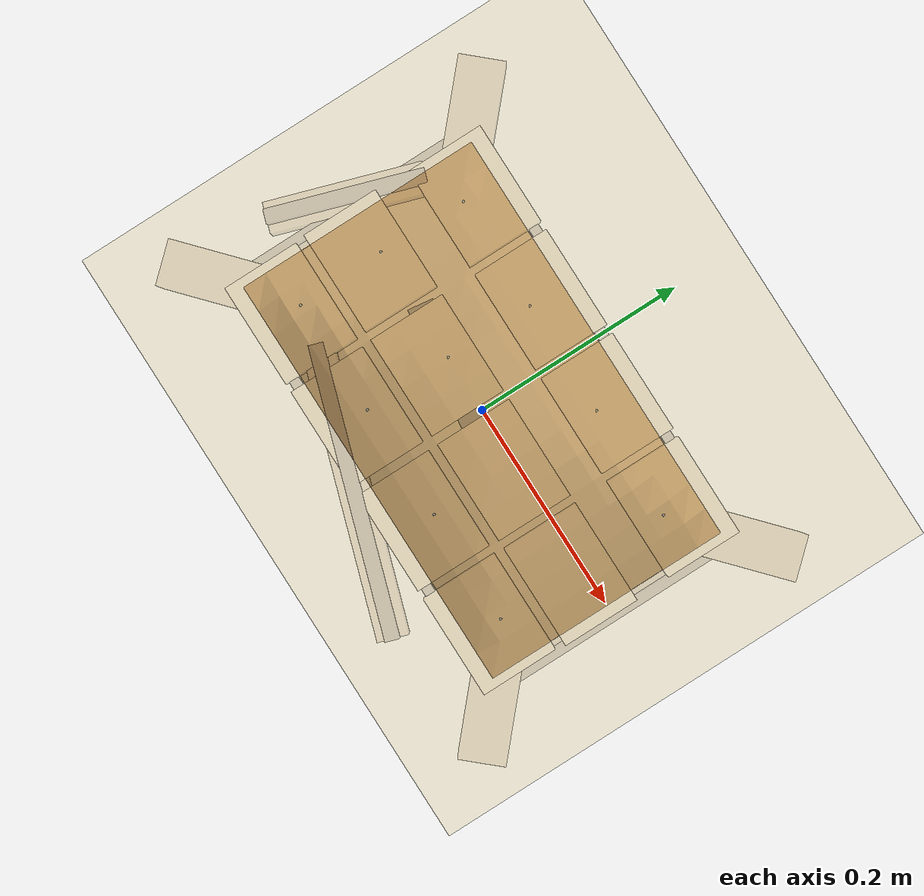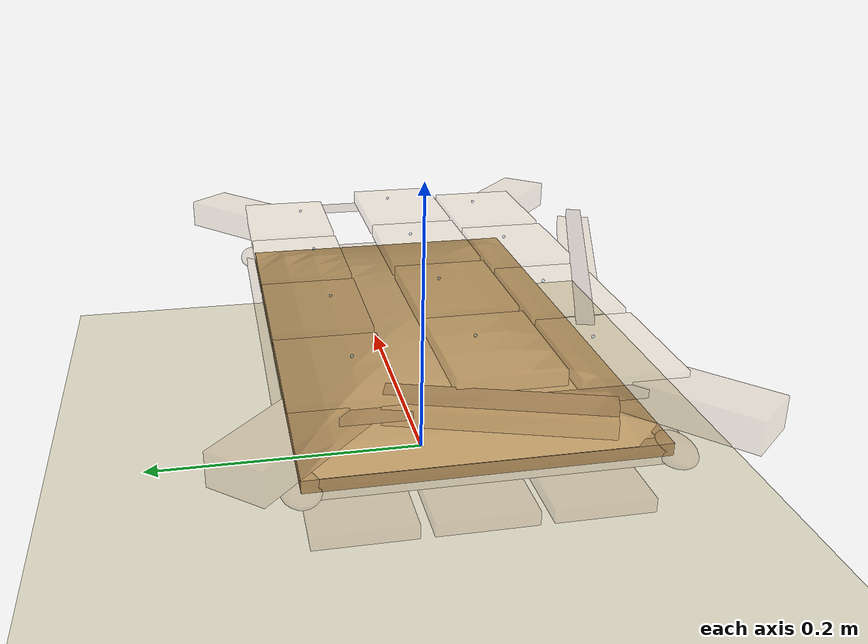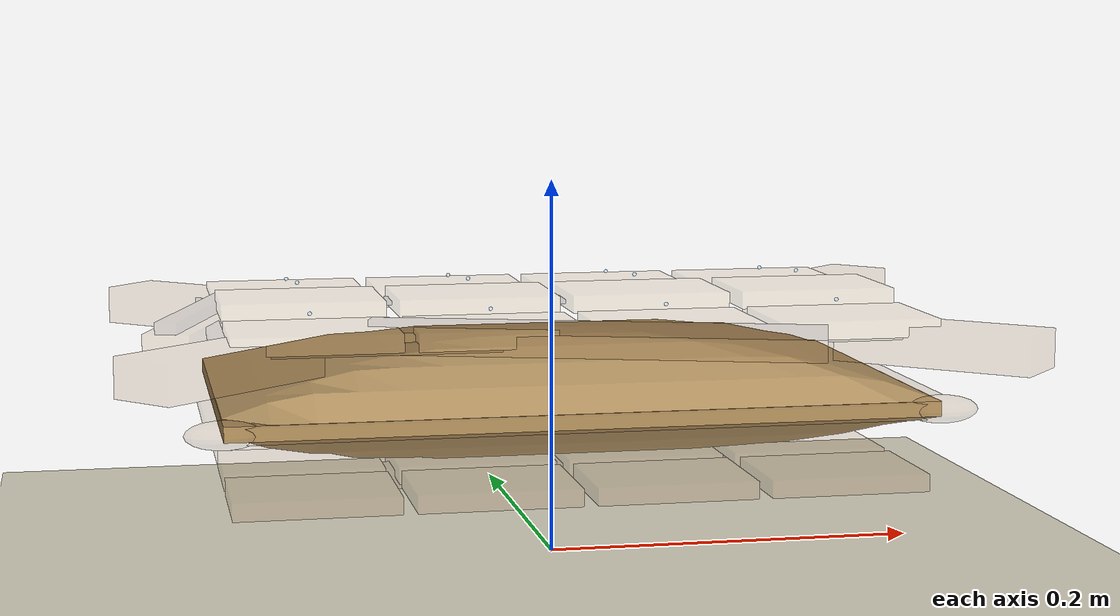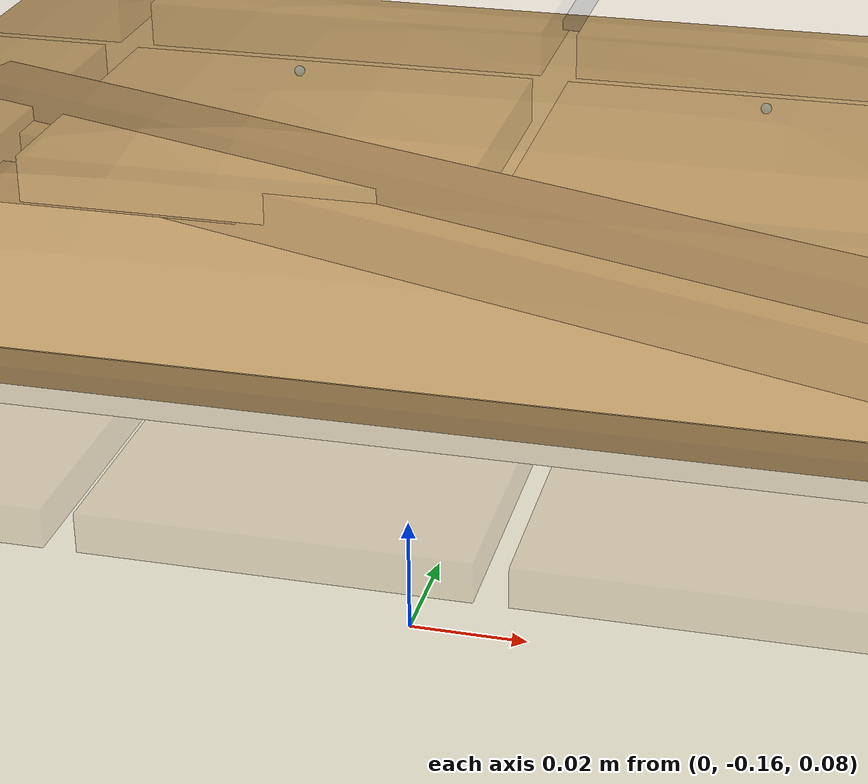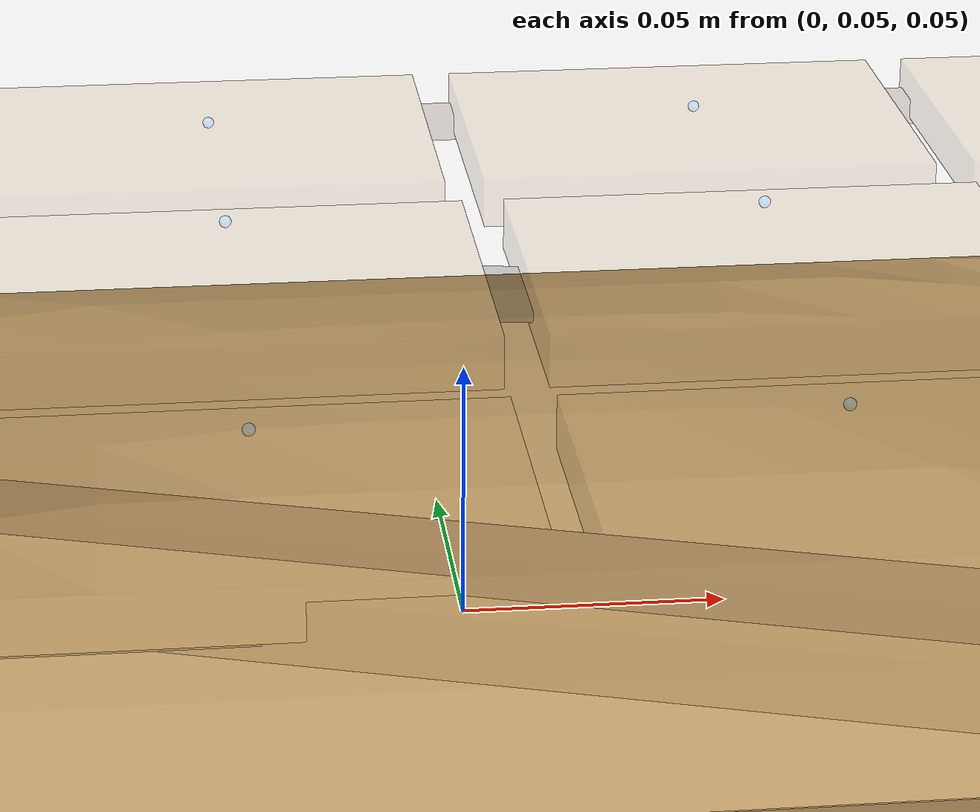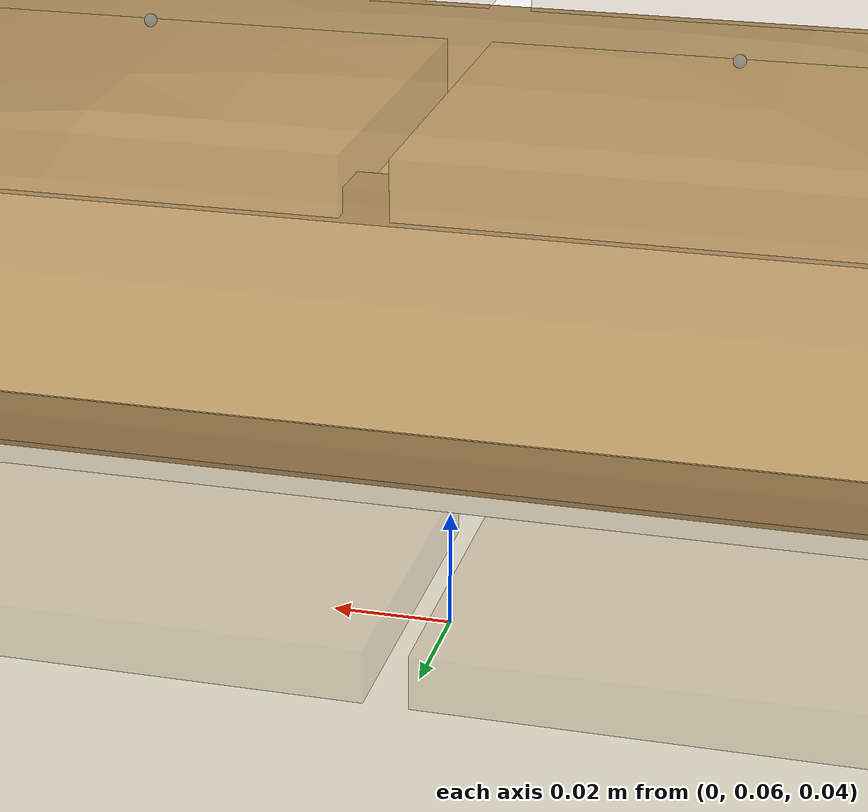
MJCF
<mujoco model="shared_flat_pillow_sack_skeleton">
  <compiler angle="degree" autolimits="true" />
  <option timestep="0.001000" gravity="0 0 -9.81" integrator="implicitfast" solver="Newton" iterations="100" ls_iterations="24" jacobian="sparse" cone="elliptic" impratio="4" />
  <size nconmax="2600" njmax="3600" />
  <visual>
    <global offwidth="1280" offheight="820" />
  </visual>
  <asset>
    <mesh name="sealed_pillow_mesh" vertex="-0.180000 -0.105000 0.003900 -0.157500 -0.105000 0.003900 -0.135000 -0.105000 0.003900 -0.112500 -0.105000 0.003900 -0.090000 -0.105000 0.003900 -0.067500 -0.105000 0.003900 -0.045000 -0.105000 0.003900 -0.022500 -0.105000 0.003900 0.000000 -0.105000 0.003900 0.022500 -0.105000 0.003900 0.045000 -0.105000 0.003900 0.067500 -0.105000 0.003900 0.090000 -0.105000 0.003900 0.112500 -0.105000 0.003900 0.135000 -0.105000 0.003900 0.157500 -0.105000 0.003900 0.180000 -0.105000 0.003900 -0.180000 -0.084000 0.003900 -0.157500 -0.084000 0.011048 -0.135000 -0.084000 0.014793 -0.112500 -0.084000 0.014793 -0.090000 -0.084000 0.014793 -0.067500 -0.084000 0.014793 -0.045000 -0.084000 0.014793 -0.022500 -0.084000 0.014793 0.000000 -0.084000 0.014793 0.022500 -0.084000 0.014793 0.045000 -0.084000 0.014793 0.067500 -0.084000 0.014793 0.090000 -0.084000 0.014793 0.112500 -0.084000 0.014793 0.135000 -0.084000 0.014793 0.157500 -0.084000 0.011048 0.180000 -0.084000 0.003900 -0.180000 -0.063000 0.003900 -0.157500 -0.063000 0.011048 -0.135000 -0.063000 0.017068 -0.112500 -0.063000 0.021995 -0.090000 -0.063000 0.022853 -0.067500 -0.063000 0.022853 -0.045000 -0.063000 0.022853 -0.022500 -0.063000 0.022853 0.000000 -0.063000 0.022853 0.022500 -0.063000 0.022853 0.045000 -0.063000 0.022853 0.067500 -0.063000 0.022853 0.090000 -0.063000 0.022853 0.112500 -0.063000 0.021995 0.135000 -0.063000 0.017068 0.157500 -0.063000 0.011048 0.180000 -0.063000 0.003900 -0.180000 -0.042000 0.003900 -0.157500 -0.042000 0.011048 -0.135000 -0.042000 0.017068 -0.112500 -0.042000 0.021995 -0.090000 -0.042000 0.025869 -0.067500 -0.042000 0.028240 -0.045000 -0.042000 0.028240 -0.022500 -0.042000 0.028240 0.000000 -0.042000 0.028240 0.022500 -0.042000 0.028240 0.045000 -0.042000 0.028240 0.067500 -0.042000 0.028240 0.090000 -0.042000 0.025869 0.112500 -0.042000 0.021995 0.135000 -0.042000 0.017068 0.157500 -0.042000 0.011048 0.180000 -0.042000 0.003900 -0.180000 -0.021000 0.003900 -0.157500 -0.021000 0.011048 -0.135000 -0.021000 0.017068 -0.112500 -0.021000 0.021995 -0.090000 -0.021000 0.025869 -0.067500 -0.021000 0.028735 -0.045000 -0.021000 0.030650 -0.022500 -0.021000 0.031166 0.000000 -0.021000 0.031166 0.022500 -0.021000 0.031166 0.045000 -0.021000 0.030650 0.067500 -0.021000 0.028735 0.090000 -0.021000 0.025869 0.112500 -0.021000 0.021995 0.135000 -0.021000 0.017068 0.157500 -0.021000 0.011048 0.180000 -0.021000 0.003900 -0.180000 0.000000 0.003900 -0.157500 0.000000 0.011048 -0.135000 0.000000 0.017068 -0.112500 0.000000 0.021995 -0.090000 0.000000 0.025869 -0.067500 0.000000 0.028735 -0.045000 0.000000 0.030650 -0.022500 0.000000 0.031691 0.000000 0.000000 0.031980 0.022500 0.000000 0.031691 0.045000 0.000000 0.030650 0.067500 0.000000 0.028735 0.090000 0.000000 0.025869 0.112500 0.000000 0.021995 0.135000 0.000000 0.017068 0.157500 0.000000 0.011048 0.180000 0.000000 0.003900 -0.180000 0.021000 0.003900 -0.157500 0.021000 0.011048 -0.135000 0.021000 0.017068 -0.112500 0.021000 0.021995 -0.090000 0.021000 0.025869 -0.067500 0.021000 0.028735 -0.045000 0.021000 0.030650 -0.022500 0.021000 0.031166 0.000000 0.021000 0.031166 0.022500 0.021000 0.031166 0.045000 0.021000 0.030650 0.067500 0.021000 0.028735 0.090000 0.021000 0.025869 0.112500 0.021000 0.021995 0.135000 0.021000 0.017068 0.157500 0.021000 0.011048 0.180000 0.021000 0.003900 -0.180000 0.042000 0.003900 -0.157500 0.042000 0.011048 -0.135000 0.042000 0.017068 -0.112500 0.042000 0.021995 -0.090000 0.042000 0.025869 -0.067500 0.042000 0.028240 -0.045000 0.042000 0.028240 -0.022500 0.042000 0.028240 0.000000 0.042000 0.028240 0.022500 0.042000 0.028240 0.045000 0.042000 0.028240 0.067500 0.042000 0.028240 0.090000 0.042000 0.025869 0.112500 0.042000 0.021995 0.135000 0.042000 0.017068 0.157500 0.042000 0.011048 0.180000 0.042000 0.003900 -0.180000 0.063000 0.003900 -0.157500 0.063000 0.011048 -0.135000 0.063000 0.017068 -0.112500 0.063000 0.021995 -0.090000 0.063000 0.022853 -0.067500 0.063000 0.022853 -0.045000 0.063000 0.022853 -0.022500 0.063000 0.022853 0.000000 0.063000 0.022853 0.022500 0.063000 0.022853 0.045000 0.063000 0.022853 0.067500 0.063000 0.022853 0.090000 0.063000 0.022853 0.112500 0.063000 0.021995 0.135000 0.063000 0.017068 0.157500 0.063000 0.011048 0.180000 0.063000 0.003900 -0.180000 0.084000 0.003900 -0.157500 0.084000 0.011048 -0.135000 0.084000 0.014793 -0.112500 0.084000 0.014793 -0.090000 0.084000 0.014793 -0.067500 0.084000 0.014793 -0.045000 0.084000 0.014793 -0.022500 0.084000 0.014793 0.000000 0.084000 0.014793 0.022500 0.084000 0.014793 0.045000 0.084000 0.014793 0.067500 0.084000 0.014793 0.090000 0.084000 0.014793 0.112500 0.084000 0.014793 0.135000 0.084000 0.014793 0.157500 0.084000 0.011048 0.180000 0.084000 0.003900 -0.180000 0.105000 0.003900 -0.157500 0.105000 0.003900 -0.135000 0.105000 0.003900 -0.112500 0.105000 0.003900 -0.090000 0.105000 0.003900 -0.067500 0.105000 0.003900 -0.045000 0.105000 0.003900 -0.022500 0.105000 0.003900 0.000000 0.105000 0.003900 0.022500 0.105000 0.003900 0.045000 0.105000 0.003900 0.067500 0.105000 0.003900 0.090000 0.105000 0.003900 0.112500 0.105000 0.003900 0.135000 0.105000 0.003900 0.157500 0.105000 0.003900 0.180000 0.105000 0.003900 -0.180000 -0.105000 -0.003900 -0.157500 -0.105000 -0.003900 -0.135000 -0.105000 -0.003900 -0.112500 -0.105000 -0.003900 -0.090000 -0.105000 -0.003900 -0.067500 -0.105000 -0.003900 -0.045000 -0.105000 -0.003900 -0.022500 -0.105000 -0.003900 0.000000 -0.105000 -0.003900 0.022500 -0.105000 -0.003900 0.045000 -0.105000 -0.003900 0.067500 -0.105000 -0.003900 0.090000 -0.105000 -0.003900 0.112500 -0.105000 -0.003900 0.135000 -0.105000 -0.003900 0.157500 -0.105000 -0.003900 0.180000 -0.105000 -0.003900 -0.180000 -0.084000 -0.003900 -0.157500 -0.084000 -0.011048 -0.135000 -0.084000 -0.014793 -0.112500 -0.084000 -0.014793 -0.090000 -0.084000 -0.014793 -0.067500 -0.084000 -0.014793 -0.045000 -0.084000 -0.014793 -0.022500 -0.084000 -0.014793 0.000000 -0.084000 -0.014793 0.022500 -0.084000 -0.014793 0.045000 -0.084000 -0.014793 0.067500 -0.084000 -0.014793 0.090000 -0.084000 -0.014793 0.112500 -0.084000 -0.014793 0.135000 -0.084000 -0.014793 0.157500 -0.084000 -0.011048 0.180000 -0.084000 -0.003900 -0.180000 -0.063000 -0.003900 -0.157500 -0.063000 -0.011048 -0.135000 -0.063000 -0.017068 -0.112500 -0.063000 -0.021995 -0.090000 -0.063000 -0.022853 -0.067500 -0.063000 -0.022853 -0.045000 -0.063000 -0.022853 -0.022500 -0.063000 -0.022853 0.000000 -0.063000 -0.022853 0.022500 -0.063000 -0.022853 0.045000 -0.063000 -0.022853 0.067500 -0.063000 -0.022853 0.090000 -0.063000 -0.022853 0.112500 -0.063000 -0.021995 0.135000 -0.063000 -0.017068 0.157500 -0.063000 -0.011048 0.180000 -0.063000 -0.003900 -0.180000 -0.042000 -0.003900 -0.157500 -0.042000 -0.011048 -0.135000 -0.042000 -0.017068 -0.112500 -0.042000 -0.021995 -0.090000 -0.042000 -0.025869 -0.067500 -0.042000 -0.028240 -0.045000 -0.042000 -0.028240 -0.022500 -0.042000 -0.028240 0.000000 -0.042000 -0.028240 0.022500 -0.042000 -0.028240 0.045000 -0.042000 -0.028240 0.067500 -0.042000 -0.028240 0.090000 -0.042000 -0.025869 0.112500 -0.042000 -0.021995 0.135000 -0.042000 -0.017068 0.157500 -0.042000 -0.011048 0.180000 -0.042000 -0.003900 -0.180000 -0.021000 -0.003900 -0.157500 -0.021000 -0.011048 -0.135000 -0.021000 -0.017068 -0.112500 -0.021000 -0.021995 -0.090000 -0.021000 -0.025869 -0.067500 -0.021000 -0.028735 -0.045000 -0.021000 -0.030650 -0.022500 -0.021000 -0.031166 0.000000 -0.021000 -0.031166 0.022500 -0.021000 -0.031166 0.045000 -0.021000 -0.030650 0.067500 -0.021000 -0.028735 0.090000 -0.021000 -0.025869 0.112500 -0.021000 -0.021995 0.135000 -0.021000 -0.017068 0.157500 -0.021000 -0.011048 0.180000 -0.021000 -0.003900 -0.180000 0.000000 -0.003900 -0.157500 0.000000 -0.011048 -0.135000 0.000000 -0.017068 -0.112500 0.000000 -0.021995 -0.090000 0.000000 -0.025869 -0.067500 0.000000 -0.028735 -0.045000 0.000000 -0.030650 -0.022500 0.000000 -0.031691 0.000000 0.000000 -0.031980 0.022500 0.000000 -0.031691 0.045000 0.000000 -0.030650 0.067500 0.000000 -0.028735 0.090000 0.000000 -0.025869 0.112500 0.000000 -0.021995 0.135000 0.000000 -0.017068 0.157500 0.000000 -0.011048 0.180000 0.000000 -0.003900 -0.180000 0.021000 -0.003900 -0.157500 0.021000 -0.011048 -0.135000 0.021000 -0.017068 -0.112500 0.021000 -0.021995 -0.090000 0.021000 -0.025869 -0.067500 0.021000 -0.028735 -0.045000 0.021000 -0.030650 -0.022500 0.021000 -0.031166 0.000000 0.021000 -0.031166 0.022500 0.021000 -0.031166 0.045000 0.021000 -0.030650 0.067500 0.021000 -0.028735 0.090000 0.021000 -0.025869 0.112500 0.021000 -0.021995 0.135000 0.021000 -0.017068 0.157500 0.021000 -0.011048 0.180000 0.021000 -0.003900 -0.180000 0.042000 -0.003900 -0.157500 0.042000 -0.011048 -0.135000 0.042000 -0.017068 -0.112500 0.042000 -0.021995 -0.090000 0.042000 -0.025869 -0.067500 0.042000 -0.028240 -0.045000 0.042000 -0.028240 -0.022500 0.042000 -0.028240 0.000000 0.042000 -0.028240 0.022500 0.042000 -0.028240 0.045000 0.042000 -0.028240 0.067500 0.042000 -0.028240 0.090000 0.042000 -0.025869 0.112500 0.042000 -0.021995 0.135000 0.042000 -0.017068 0.157500 0.042000 -0.011048 0.180000 0.042000 -0.003900 -0.180000 0.063000 -0.003900 -0.157500 0.063000 -0.011048 -0.135000 0.063000 -0.017068 -0.112500 0.063000 -0.021995 -0.090000 0.063000 -0.022853 -0.067500 0.063000 -0.022853 -0.045000 0.063000 -0.022853 -0.022500 0.063000 -0.022853 0.000000 0.063000 -0.022853 0.022500 0.063000 -0.022853 0.045000 0.063000 -0.022853 0.067500 0.063000 -0.022853 0.090000 0.063000 -0.022853 0.112500 0.063000 -0.021995 0.135000 0.063000 -0.017068 0.157500 0.063000 -0.011048 0.180000 0.063000 -0.003900 -0.180000 0.084000 -0.003900 -0.157500 0.084000 -0.011048 -0.135000 0.084000 -0.014793 -0.112500 0.084000 -0.014793 -0.090000 0.084000 -0.014793 -0.067500 0.084000 -0.014793 -0.045000 0.084000 -0.014793 -0.022500 0.084000 -0.014793 0.000000 0.084000 -0.014793 0.022500 0.084000 -0.014793 0.045000 0.084000 -0.014793 0.067500 0.084000 -0.014793 0.090000 0.084000 -0.014793 0.112500 0.084000 -0.014793 0.135000 0.084000 -0.014793 0.157500 0.084000 -0.011048 0.180000 0.084000 -0.003900 -0.180000 0.105000 -0.003900 -0.157500 0.105000 -0.003900 -0.135000 0.105000 -0.003900 -0.112500 0.105000 -0.003900 -0.090000 0.105000 -0.003900 -0.067500 0.105000 -0.003900 -0.045000 0.105000 -0.003900 -0.022500 0.105000 -0.003900 0.000000 0.105000 -0.003900 0.022500 0.105000 -0.003900 0.045000 0.105000 -0.003900 0.067500 0.105000 -0.003900 0.090000 0.105000 -0.003900 0.112500 0.105000 -0.003900 0.135000 0.105000 -0.003900 0.157500 0.105000 -0.003900 0.180000 0.105000 -0.003900" face="0 1 17 1 18 17 187 204 188 188 204 205 1 2 18 2 19 18 188 205 189 189 205 206 2 3 19 3 20 19 189 206 190 190 206 207 3 4 20 4 21 20 190 207 191 191 207 208 4 5 21 5 22 21 191 208 192 192 208 209 5 6 22 6 23 22 192 209 193 193 209 210 6 7 23 7 24 23 193 210 194 194 210 211 7 8 24 8 25 24 194 211 195 195 211 212 8 9 25 9 26 25 195 212 196 196 212 213 9 10 26 10 27 26 196 213 197 197 213 214 10 11 27 11 28 27 197 214 198 198 214 215 11 12 28 12 29 28 198 215 199 199 215 216 12 13 29 13 30 29 199 216 200 200 216 217 13 14 30 14 31 30 200 217 201 201 217 218 14 15 31 15 32 31 201 218 202 202 218 219 15 16 32 16 33 32 202 219 203 203 219 220 17 18 34 18 35 34 204 221 205 205 221 222 18 19 35 19 36 35 205 222 206 206 222 223 19 20 36 20 37 36 206 223 207 207 223 224 20 21 37 21 38 37 207 224 208 208 224 225 21 22 38 22 39 38 208 225 209 209 225 226 22 23 39 23 40 39 209 226 210 210 226 227 23 24 40 24 41 40 210 227 211 211 227 228 24 25 41 25 42 41 211 228 212 212 228 229 25 26 42 26 43 42 212 229 213 213 229 230 26 27 43 27 44 43 213 230 214 214 230 231 27 28 44 28 45 44 214 231 215 215 231 232 28 29 45 29 46 45 215 232 216 216 232 233 29 30 46 30 47 46 216 233 217 217 233 234 30 31 47 31 48 47 217 234 218 218 234 235 31 32 48 32 49 48 218 235 219 219 235 236 32 33 49 33 50 49 219 236 220 220 236 237 34 35 51 35 52 51 221 238 222 222 238 239 35 36 52 36 53 52 222 239 223 223 239 240 36 37 53 37 54 53 223 240 224 224 240 241 37 38 54 38 55 54 224 241 225 225 241 242 38 39 55 39 56 55 225 242 226 226 242 243 39 40 56 40 57 56 226 243 227 227 243 244 40 41 57 41 58 57 227 244 228 228 244 245 41 42 58 42 59 58 228 245 229 229 245 246 42 43 59 43 60 59 229 246 230 230 246 247 43 44 60 44 61 60 230 247 231 231 247 248 44 45 61 45 62 61 231 248 232 232 248 249 45 46 62 46 63 62 232 249 233 233 249 250 46 47 63 47 64 63 233 250 234 234 250 251 47 48 64 48 65 64 234 251 235 235 251 252 48 49 65 49 66 65 235 252 236 236 252 253 49 50 66 50 67 66 236 253 237 237 253 254 51 52 68 52 69 68 238 255 239 239 255 256 52 53 69 53 70 69 239 256 240 240 256 257 53 54 70 54 71 70 240 257 241 241 257 258 54 55 71 55 72 71 241 258 242 242 258 259 55 56 72 56 73 72 242 259 243 243 259 260 56 57 73 57 74 73 243 260 244 244 260 261 57 58 74 58 75 74 244 261 245 245 261 262 58 59 75 59 76 75 245 262 246 246 262 263 59 60 76 60 77 76 246 263 247 247 263 264 60 61 77 61 78 77 247 264 248 248 264 265 61 62 78 62 79 78 248 265 249 249 265 266 62 63 79 63 80 79 249 266 250 250 266 267 63 64 80 64 81 80 250 267 251 251 267 268 64 65 81 65 82 81 251 268 252 252 268 269 65 66 82 66 83 82 252 269 253 253 269 270 66 67 83 67 84 83 253 270 254 254 270 271 68 69 85 69 86 85 255 272 256 256 272 273 69 70 86 70 87 86 256 273 257 257 273 274 70 71 87 71 88 87 257 274 258 258 274 275 71 72 88 72 89 88 258 275 259 259 275 276 72 73 89 73 90 89 259 276 260 260 276 277 73 74 90 74 91 90 260 277 261 261 277 278 74 75 91 75 92 91 261 278 262 262 278 279 75 76 92 76 93 92 262 279 263 263 279 280 76 77 93 77 94 93 263 280 264 264 280 281 77 78 94 78 95 94 264 281 265 265 281 282 78 79 95 79 96 95 265 282 266 266 282 283 79 80 96 80 97 96 266 283 267 267 283 284 80 81 97 81 98 97 267 284 268 268 284 285 81 82 98 82 99 98 268 285 269 269 285 286 82 83 99 83 100 99 269 286 270 270 286 287 83 84 100 84 101 100 270 287 271 271 287 288 85 86 102 86 103 102 272 289 273 273 289 290 86 87 103 87 104 103 273 290 274 274 290 291 87 88 104 88 105 104 274 291 275 275 291 292 88 89 105 89 106 105 275 292 276 276 292 293 89 90 106 90 107 106 276 293 277 277 293 294 90 91 107 91 108 107 277 294 278 278 294 295 91 92 108 92 109 108 278 295 279 279 295 296 92 93 109 93 110 109 279 296 280 280 296 297 93 94 110 94 111 110 280 297 281 281 297 298 94 95 111 95 112 111 281 298 282 282 298 299 95 96 112 96 113 112 282 299 283 283 299 300 96 97 113 97 114 113 283 300 284 284 300 301 97 98 114 98 115 114 284 301 285 285 301 302 98 99 115 99 116 115 285 302 286 286 302 303 99 100 116 100 117 116 286 303 287 287 303 304 100 101 117 101 118 117 287 304 288 288 304 305 102 103 119 103 120 119 289 306 290 290 306 307 103 104 120 104 121 120 290 307 291 291 307 308 104 105 121 105 122 121 291 308 292 292 308 309 105 106 122 106 123 122 292 309 293 293 309 310 106 107 123 107 124 123 293 310 294 294 310 311 107 108 124 108 125 124 294 311 295 295 311 312 108 109 125 109 126 125 295 312 296 296 312 313 109 110 126 110 127 126 296 313 297 297 313 314 110 111 127 111 128 127 297 314 298 298 314 315 111 112 128 112 129 128 298 315 299 299 315 316 112 113 129 113 130 129 299 316 300 300 316 317 113 114 130 114 131 130 300 317 301 301 317 318 114 115 131 115 132 131 301 318 302 302 318 319 115 116 132 116 133 132 302 319 303 303 319 320 116 117 133 117 134 133 303 320 304 304 320 321 117 118 134 118 135 134 304 321 305 305 321 322 119 120 136 120 137 136 306 323 307 307 323 324 120 121 137 121 138 137 307 324 308 308 324 325 121 122 138 122 139 138 308 325 309 309 325 326 122 123 139 123 140 139 309 326 310 310 326 327 123 124 140 124 141 140 310 327 311 311 327 328 124 125 141 125 142 141 311 328 312 312 328 329 125 126 142 126 143 142 312 329 313 313 329 330 126 127 143 127 144 143 313 330 314 314 330 331 127 128 144 128 145 144 314 331 315 315 331 332 128 129 145 129 146 145 315 332 316 316 332 333 129 130 146 130 147 146 316 333 317 317 333 334 130 131 147 131 148 147 317 334 318 318 334 335 131 132 148 132 149 148 318 335 319 319 335 336 132 133 149 133 150 149 319 336 320 320 336 337 133 134 150 134 151 150 320 337 321 321 337 338 134 135 151 135 152 151 321 338 322 322 338 339 136 137 153 137 154 153 323 340 324 324 340 341 137 138 154 138 155 154 324 341 325 325 341 342 138 139 155 139 156 155 325 342 326 326 342 343 139 140 156 140 157 156 326 343 327 327 343 344 140 141 157 141 158 157 327 344 328 328 344 345 141 142 158 142 159 158 328 345 329 329 345 346 142 143 159 143 160 159 329 346 330 330 346 347 143 144 160 144 161 160 330 347 331 331 347 348 144 145 161 145 162 161 331 348 332 332 348 349 145 146 162 146 163 162 332 349 333 333 349 350 146 147 163 147 164 163 333 350 334 334 350 351 147 148 164 148 165 164 334 351 335 335 351 352 148 149 165 149 166 165 335 352 336 336 352 353 149 150 166 150 167 166 336 353 337 337 353 354 150 151 167 151 168 167 337 354 338 338 354 355 151 152 168 152 169 168 338 355 339 339 355 356 153 154 170 154 171 170 340 357 341 341 357 358 154 155 171 155 172 171 341 358 342 342 358 359 155 156 172 156 173 172 342 359 343 343 359 360 156 157 173 157 174 173 343 360 344 344 360 361 157 158 174 158 175 174 344 361 345 345 361 362 158 159 175 159 176 175 345 362 346 346 362 363 159 160 176 160 177 176 346 363 347 347 363 364 160 161 177 161 178 177 347 364 348 348 364 365 161 162 178 162 179 178 348 365 349 349 365 366 162 163 179 163 180 179 349 366 350 350 366 367 163 164 180 164 181 180 350 367 351 351 367 368 164 165 181 165 182 181 351 368 352 352 368 369 165 166 182 166 183 182 352 369 353 353 369 370 166 167 183 167 184 183 353 370 354 354 370 371 167 168 184 168 185 184 354 371 355 355 371 372 168 169 185 169 186 185 355 372 356 356 372 373 0 187 1 1 187 188 170 171 357 171 358 357 1 188 2 2 188 189 171 172 358 172 359 358 2 189 3 3 189 190 172 173 359 173 360 359 3 190 4 4 190 191 173 174 360 174 361 360 4 191 5 5 191 192 174 175 361 175 362 361 5 192 6 6 192 193 175 176 362 176 363 362 6 193 7 7 193 194 176 177 363 177 364 363 7 194 8 8 194 195 177 178 364 178 365 364 8 195 9 9 195 196 178 179 365 179 366 365 9 196 10 10 196 197 179 180 366 180 367 366 10 197 11 11 197 198 180 181 367 181 368 367 11 198 12 12 198 199 181 182 368 182 369 368 12 199 13 13 199 200 182 183 369 183 370 369 13 200 14 14 200 201 183 184 370 184 371 370 14 201 15 15 201 202 184 185 371 185 372 371 15 202 16 16 202 203 185 186 372 186 373 372 0 17 187 17 204 187 16 203 33 33 203 220 17 34 204 34 221 204 33 220 50 50 220 237 34 51 221 51 238 221 50 237 67 67 237 254 51 68 238 68 255 238 67 254 84 84 254 271 68 85 255 85 272 255 84 271 101 101 271 288 85 102 272 102 289 272 101 288 118 118 288 305 102 119 289 119 306 289 118 305 135 135 305 322 119 136 306 136 323 306 135 322 152 152 322 339 136 153 323 153 340 323 152 339 169 169 339 356 153 170 340 170 357 340 169 356 186 186 356 373" />
    <material name="mat_jute_skin" rgba="0.72 0.59 0.39 0.96" />
    <material name="mat_hidden_panel" rgba="0.64 0.46 0.26 0.015" />
    <material name="mat_surface_patch" rgba="0.78 0.62 0.39 0.12" />
    <material name="mat_edge_seam" rgba="0.34 0.21 0.10 0.14" />
    <material name="mat_wrinkle" rgba="0.22 0.12 0.04 0.00" />
  </asset>
  <worldbody>
    <geom group="0" friction="1.55 0.05 0.005" condim="4" solref="0.032 1" solimp="0.78 0.94 0.001" name="floor" type="plane" size="2.2 2.2 0.05" rgba="0.90 0.88 0.80 0.25" />
    <light name="key_light" pos="0.4 -0.7 1.3" dir="-0.2 0.35 -1" />
    <camera name="front" pos="0.56 -0.62 0.28" xyaxes="0.74 0.67 0 -0.18 0.20 0.96" />
    <camera name="side" pos="0 -0.62 0.20" xyaxes="1 0 0 0 0.16 0.99" />
    <camera name="top_angled" pos="0.34 -0.46 0.48" xyaxes="0.80 0.60 0 -0.45 0.60 0.66" />
    <body name="bag_frame" pos="0 0 0.090000">
      <freejoint name="bag_frame_freejoint" />
      <site name="bag_frame_origin" pos="0 0 0" size="0.001" rgba="1 0 0 0.05" />
      <geom group="1" friction="1.45 0.06 0.006" condim="4" solref="0.032 1" solimp="0.78 0.94 0.001" name="bag_mouse_handle" type="sphere" pos="0 0 0" size="0.025" mass="0.001" rgba="0.10 0.35 1.00 0.02" contype="0" conaffinity="0" />
      <body name="visual_skin" pos="0 0 0">
        <geom group="0" friction="1.45 0.06 0.006" condim="4" solref="0.032 1" solimp="0.78 0.94 0.001" name="visual_skin_main_pillow" type="mesh" mesh="sealed_pillow_mesh" material="mat_jute_skin" contype="0" conaffinity="0" mass="0.001" />
        <body name="visual_front_edge_seam" pos="0.000000 -0.105000 0.000000" euler="0 0 0">
          <geom group="0" friction="1.45 0.06 0.006" condim="4" solref="0.032 1" solimp="0.78 0.94 0.001" name="visual_front_edge_seam_geom" type="box" size="0.176400 0.007500 0.004000" rgba="0.55 0.39 0.20 0.16" contype="0" conaffinity="0" mass="0.001" />
        </body>
        <body name="visual_back_edge_seam" pos="0.000000 0.105000 0.000000" euler="0 0 0">
          <geom group="0" friction="1.45 0.06 0.006" condim="4" solref="0.032 1" solimp="0.78 0.94 0.001" name="visual_back_edge_seam_geom" type="box" size="0.176400 0.007500 0.004000" rgba="0.55 0.39 0.20 0.16" contype="0" conaffinity="0" mass="0.001" />
        </body>
        <body name="visual_left_edge_seam" pos="-0.180000 0.000000 0.000000" euler="0 0 90">
          <geom group="0" friction="1.45 0.06 0.006" condim="4" solref="0.032 1" solimp="0.78 0.94 0.001" name="visual_left_edge_seam_geom" type="box" size="0.102900 0.007500 0.004000" rgba="0.55 0.39 0.20 0.16" contype="0" conaffinity="0" mass="0.001" />
        </body>
        <body name="visual_right_edge_seam" pos="0.180000 0.000000 0.000000" euler="0 0 90">
          <geom group="0" friction="1.45 0.06 0.006" condim="4" solref="0.032 1" solimp="0.78 0.94 0.001" name="visual_right_edge_seam_geom" type="box" size="0.102900 0.007500 0.004000" rgba="0.55 0.39 0.20 0.16" contype="0" conaffinity="0" mass="0.001" />
        </body>
        <body name="visual_corner_front_left" pos="-0.180000 -0.105000 0.000000">
          <geom group="0" friction="1.45 0.06 0.006" condim="4" solref="0.032 1" solimp="0.78 0.94 0.001" name="visual_corner_front_left_geom" type="ellipsoid" size="0.019 0.012 0.007" rgba="0.56 0.40 0.22 0.025" contype="0" conaffinity="0" mass="0.001" />
        </body>
        <body name="visual_corner_front_right" pos="0.180000 -0.105000 0.000000">
          <geom group="0" friction="1.45 0.06 0.006" condim="4" solref="0.032 1" solimp="0.78 0.94 0.001" name="visual_corner_front_right_geom" type="ellipsoid" size="0.019 0.012 0.007" rgba="0.56 0.40 0.22 0.025" contype="0" conaffinity="0" mass="0.001" />
        </body>
        <body name="visual_corner_back_left" pos="-0.180000 0.105000 0.000000">
          <geom group="0" friction="1.45 0.06 0.006" condim="4" solref="0.032 1" solimp="0.78 0.94 0.001" name="visual_corner_back_left_geom" type="ellipsoid" size="0.019 0.012 0.007" rgba="0.56 0.40 0.22 0.025" contype="0" conaffinity="0" mass="0.001" />
        </body>
        <body name="visual_corner_back_right" pos="0.180000 0.105000 0.000000">
          <geom group="0" friction="1.45 0.06 0.006" condim="4" solref="0.032 1" solimp="0.78 0.94 0.001" name="visual_corner_back_right_geom" type="ellipsoid" size="0.019 0.012 0.007" rgba="0.56 0.40 0.22 0.025" contype="0" conaffinity="0" mass="0.001" />
        </body>
        <body name="visual_print_mark" pos="-0.030 -0.005 0.048" euler="0 0 -8">
          <geom group="0" friction="1.45 0.06 0.006" condim="4" solref="0.032 1" solimp="0.78 0.94 0.001" name="visual_print_mark_geom" type="box" size="0.060 0.010 0.001" rgba="0.08 0.08 0.07 0.22" contype="0" conaffinity="0" mass="0.001" />
        </body>
        <body name="sealed_top_cap_visual" pos="0 0 0.052">
          <geom group="0" friction="1.45 0.06 0.006" condim="4" solref="0.032 1" solimp="0.78 0.94 0.001" name="sealed_top_cap_visual_geom" type="ellipsoid" size="0.122400 0.063000 0.004000" rgba="0.74 0.57 0.34 0.00" contype="0" conaffinity="0" mass="0.001" />
        </body>
      </body>
      <body name="top_surface_panels" pos="0 0 0">
        <body name="top_panel_00" pos="-0.135000 -0.070000 0.042333">
          <joint name="top_panel_00_hinge" type="hinge" axis="1 0 0" limited="true" range="-28 28" damping="7.500" stiffness="1.600" />
          <geom group="1" friction="1.45 0.06 0.006" condim="4" solref="0.032 1" solimp="0.78 0.94 0.001" name="top_panel_00_geom" type="box" pos="0 -0.010000 0.000000" size="0.041400 0.030800 0.004500" mass="0.026" material="mat_surface_patch" />
          <geom group="1" friction="1.45 0.06 0.006" condim="4" solref="0.032 1" solimp="0.78 0.94 0.001" name="top_panel_00_cloth_visual" type="ellipsoid" pos="0 0 0.006500" size="0.039600 0.029400 0.002500" rgba="0.74 0.58 0.36 0.00" contype="0" conaffinity="0" mass="0.0002" />
          <geom group="1" friction="1.45 0.06 0.006" condim="4" solref="0.032 1" solimp="0.78 0.94 0.001" name="top_panel_00_wrinkle_0" type="capsule" fromto="-0.034200 -0.016800 0.006 0.034200 -0.010920 0.006" size="0.0008" material="mat_wrinkle" contype="0" conaffinity="0" mass="0.0002" />
          <geom group="1" friction="1.45 0.06 0.006" condim="4" solref="0.032 1" solimp="0.78 0.94 0.001" name="top_panel_00_wrinkle_1" type="capsule" fromto="-0.034200 0.000000 0.006 0.034200 0.000000 0.006" size="0.0008" material="mat_wrinkle" contype="0" conaffinity="0" mass="0.0002" />
          <geom group="1" friction="1.45 0.06 0.006" condim="4" solref="0.032 1" solimp="0.78 0.94 0.001" name="top_panel_00_wrinkle_2" type="capsule" fromto="-0.034200 0.016800 0.006 0.034200 0.010920 0.006" size="0.0008" material="mat_wrinkle" contype="0" conaffinity="0" mass="0.0002" />
          <site name="grasp_top_panel_00" pos="0 0 0.010" size="0.001" rgba="0.1 0.6 1 0.05" />
        </body>
        <body name="top_panel_01" pos="-0.135000 -0.000000 0.049000">
          <joint name="top_panel_01_hinge" type="hinge" axis="1 0 0" limited="true" range="-28 28" damping="7.500" stiffness="1.600" />
          <geom group="1" friction="1.45 0.06 0.006" condim="4" solref="0.032 1" solimp="0.78 0.94 0.001" name="top_panel_01_geom" type="box" pos="0 -0.010000 0.000000" size="0.041400 0.030800 0.004500" mass="0.026" material="mat_surface_patch" />
          <geom group="1" friction="1.45 0.06 0.006" condim="4" solref="0.032 1" solimp="0.78 0.94 0.001" name="top_panel_01_cloth_visual" type="ellipsoid" pos="0 0 0.006500" size="0.039600 0.029400 0.002500" rgba="0.74 0.58 0.36 0.00" contype="0" conaffinity="0" mass="0.0002" />
          <geom group="1" friction="1.45 0.06 0.006" condim="4" solref="0.032 1" solimp="0.78 0.94 0.001" name="top_panel_01_wrinkle_0" type="capsule" fromto="-0.034200 -0.016800 0.006 0.034200 -0.010920 0.006" size="0.0008" material="mat_wrinkle" contype="0" conaffinity="0" mass="0.0002" />
          <geom group="1" friction="1.45 0.06 0.006" condim="4" solref="0.032 1" solimp="0.78 0.94 0.001" name="top_panel_01_wrinkle_1" type="capsule" fromto="-0.034200 0.000000 0.006 0.034200 0.000000 0.006" size="0.0008" material="mat_wrinkle" contype="0" conaffinity="0" mass="0.0002" />
          <geom group="1" friction="1.45 0.06 0.006" condim="4" solref="0.032 1" solimp="0.78 0.94 0.001" name="top_panel_01_wrinkle_2" type="capsule" fromto="-0.034200 0.016800 0.006 0.034200 0.010920 0.006" size="0.0008" material="mat_wrinkle" contype="0" conaffinity="0" mass="0.0002" />
          <site name="grasp_top_panel_01" pos="0 0 0.010" size="0.001" rgba="0.1 0.6 1 0.05" />
        </body>
        <body name="top_panel_02" pos="-0.135000 0.070000 0.042333">
          <joint name="top_panel_02_hinge" type="hinge" axis="1 0 0" limited="true" range="-28 28" damping="7.500" stiffness="1.600" />
          <geom group="1" friction="1.45 0.06 0.006" condim="4" solref="0.032 1" solimp="0.78 0.94 0.001" name="top_panel_02_geom" type="box" pos="0 0.010000 0.000000" size="0.041400 0.030800 0.004500" mass="0.026" material="mat_surface_patch" />
          <geom group="1" friction="1.45 0.06 0.006" condim="4" solref="0.032 1" solimp="0.78 0.94 0.001" name="top_panel_02_cloth_visual" type="ellipsoid" pos="0 0 0.006500" size="0.039600 0.029400 0.002500" rgba="0.74 0.58 0.36 0.00" contype="0" conaffinity="0" mass="0.0002" />
          <geom group="1" friction="1.45 0.06 0.006" condim="4" solref="0.032 1" solimp="0.78 0.94 0.001" name="top_panel_02_wrinkle_0" type="capsule" fromto="-0.034200 -0.016800 0.006 0.034200 -0.010920 0.006" size="0.0008" material="mat_wrinkle" contype="0" conaffinity="0" mass="0.0002" />
          <geom group="1" friction="1.45 0.06 0.006" condim="4" solref="0.032 1" solimp="0.78 0.94 0.001" name="top_panel_02_wrinkle_1" type="capsule" fromto="-0.034200 0.000000 0.006 0.034200 0.000000 0.006" size="0.0008" material="mat_wrinkle" contype="0" conaffinity="0" mass="0.0002" />
          <geom group="1" friction="1.45 0.06 0.006" condim="4" solref="0.032 1" solimp="0.78 0.94 0.001" name="top_panel_02_wrinkle_2" type="capsule" fromto="-0.034200 0.016800 0.006 0.034200 0.010920 0.006" size="0.0008" material="mat_wrinkle" contype="0" conaffinity="0" mass="0.0002" />
          <site name="grasp_top_panel_02" pos="0 0 0.010" size="0.001" rgba="0.1 0.6 1 0.05" />
        </body>
        <body name="top_panel_03" pos="-0.045000 -0.070000 0.042333">
          <joint name="top_panel_03_hinge" type="hinge" axis="1 0 0" limited="true" range="-28 28" damping="7.500" stiffness="1.600" />
          <geom group="1" friction="1.45 0.06 0.006" condim="4" solref="0.032 1" solimp="0.78 0.94 0.001" name="top_panel_03_geom" type="box" pos="0 -0.010000 0.000000" size="0.041400 0.030800 0.004500" mass="0.026" material="mat_surface_patch" />
          <geom group="1" friction="1.45 0.06 0.006" condim="4" solref="0.032 1" solimp="0.78 0.94 0.001" name="top_panel_03_cloth_visual" type="ellipsoid" pos="0 0 0.006500" size="0.039600 0.029400 0.002500" rgba="0.74 0.58 0.36 0.00" contype="0" conaffinity="0" mass="0.0002" />
          <geom group="1" friction="1.45 0.06 0.006" condim="4" solref="0.032 1" solimp="0.78 0.94 0.001" name="top_panel_03_wrinkle_0" type="capsule" fromto="-0.034200 -0.016800 0.006 0.034200 -0.010920 0.006" size="0.0008" material="mat_wrinkle" contype="0" conaffinity="0" mass="0.0002" />
          <geom group="1" friction="1.45 0.06 0.006" condim="4" solref="0.032 1" solimp="0.78 0.94 0.001" name="top_panel_03_wrinkle_1" type="capsule" fromto="-0.034200 0.000000 0.006 0.034200 0.000000 0.006" size="0.0008" material="mat_wrinkle" contype="0" conaffinity="0" mass="0.0002" />
          <geom group="1" friction="1.45 0.06 0.006" condim="4" solref="0.032 1" solimp="0.78 0.94 0.001" name="top_panel_03_wrinkle_2" type="capsule" fromto="-0.034200 0.016800 0.006 0.034200 0.010920 0.006" size="0.0008" material="mat_wrinkle" contype="0" conaffinity="0" mass="0.0002" />
          <site name="grasp_top_panel_03" pos="0 0 0.010" size="0.001" rgba="0.1 0.6 1 0.05" />
        </body>
        <body name="top_panel_04" pos="-0.045000 -0.000000 0.049000">
          <joint name="top_panel_04_hinge" type="hinge" axis="1 0 0" limited="true" range="-28 28" damping="7.500" stiffness="1.600" />
          <geom group="1" friction="1.45 0.06 0.006" condim="4" solref="0.032 1" solimp="0.78 0.94 0.001" name="top_panel_04_geom" type="box" pos="0 -0.010000 0.000000" size="0.041400 0.030800 0.004500" mass="0.026" material="mat_surface_patch" />
          <geom group="1" friction="1.45 0.06 0.006" condim="4" solref="0.032 1" solimp="0.78 0.94 0.001" name="top_panel_04_cloth_visual" type="ellipsoid" pos="0 0 0.006500" size="0.039600 0.029400 0.002500" rgba="0.74 0.58 0.36 0.00" contype="0" conaffinity="0" mass="0.0002" />
          <geom group="1" friction="1.45 0.06 0.006" condim="4" solref="0.032 1" solimp="0.78 0.94 0.001" name="top_panel_04_wrinkle_0" type="capsule" fromto="-0.034200 -0.016800 0.006 0.034200 -0.010920 0.006" size="0.0008" material="mat_wrinkle" contype="0" conaffinity="0" mass="0.0002" />
          <geom group="1" friction="1.45 0.06 0.006" condim="4" solref="0.032 1" solimp="0.78 0.94 0.001" name="top_panel_04_wrinkle_1" type="capsule" fromto="-0.034200 0.000000 0.006 0.034200 0.000000 0.006" size="0.0008" material="mat_wrinkle" contype="0" conaffinity="0" mass="0.0002" />
          <geom group="1" friction="1.45 0.06 0.006" condim="4" solref="0.032 1" solimp="0.78 0.94 0.001" name="top_panel_04_wrinkle_2" type="capsule" fromto="-0.034200 0.016800 0.006 0.034200 0.010920 0.006" size="0.0008" material="mat_wrinkle" contype="0" conaffinity="0" mass="0.0002" />
          <site name="grasp_top_panel_04" pos="0 0 0.010" size="0.001" rgba="0.1 0.6 1 0.05" />
        </body>
        <body name="top_panel_05" pos="-0.045000 0.070000 0.042333">
          <joint name="top_panel_05_hinge" type="hinge" axis="1 0 0" limited="true" range="-28 28" damping="7.500" stiffness="1.600" />
          <geom group="1" friction="1.45 0.06 0.006" condim="4" solref="0.032 1" solimp="0.78 0.94 0.001" name="top_panel_05_geom" type="box" pos="0 0.010000 0.000000" size="0.041400 0.030800 0.004500" mass="0.026" material="mat_surface_patch" />
          <geom group="1" friction="1.45 0.06 0.006" condim="4" solref="0.032 1" solimp="0.78 0.94 0.001" name="top_panel_05_cloth_visual" type="ellipsoid" pos="0 0 0.006500" size="0.039600 0.029400 0.002500" rgba="0.74 0.58 0.36 0.00" contype="0" conaffinity="0" mass="0.0002" />
          <geom group="1" friction="1.45 0.06 0.006" condim="4" solref="0.032 1" solimp="0.78 0.94 0.001" name="top_panel_05_wrinkle_0" type="capsule" fromto="-0.034200 -0.016800 0.006 0.034200 -0.010920 0.006" size="0.0008" material="mat_wrinkle" contype="0" conaffinity="0" mass="0.0002" />
          <geom group="1" friction="1.45 0.06 0.006" condim="4" solref="0.032 1" solimp="0.78 0.94 0.001" name="top_panel_05_wrinkle_1" type="capsule" fromto="-0.034200 0.000000 0.006 0.034200 0.000000 0.006" size="0.0008" material="mat_wrinkle" contype="0" conaffinity="0" mass="0.0002" />
          <geom group="1" friction="1.45 0.06 0.006" condim="4" solref="0.032 1" solimp="0.78 0.94 0.001" name="top_panel_05_wrinkle_2" type="capsule" fromto="-0.034200 0.016800 0.006 0.034200 0.010920 0.006" size="0.0008" material="mat_wrinkle" contype="0" conaffinity="0" mass="0.0002" />
          <site name="grasp_top_panel_05" pos="0 0 0.010" size="0.001" rgba="0.1 0.6 1 0.05" />
        </body>
        <body name="top_panel_06" pos="0.045000 -0.070000 0.042333">
          <joint name="top_panel_06_hinge" type="hinge" axis="1 0 0" limited="true" range="-28 28" damping="7.500" stiffness="1.600" />
          <geom group="1" friction="1.45 0.06 0.006" condim="4" solref="0.032 1" solimp="0.78 0.94 0.001" name="top_panel_06_geom" type="box" pos="0 -0.010000 0.000000" size="0.041400 0.030800 0.004500" mass="0.026" material="mat_surface_patch" />
          <geom group="1" friction="1.45 0.06 0.006" condim="4" solref="0.032 1" solimp="0.78 0.94 0.001" name="top_panel_06_cloth_visual" type="ellipsoid" pos="0 0 0.006500" size="0.039600 0.029400 0.002500" rgba="0.74 0.58 0.36 0.00" contype="0" conaffinity="0" mass="0.0002" />
          <geom group="1" friction="1.45 0.06 0.006" condim="4" solref="0.032 1" solimp="0.78 0.94 0.001" name="top_panel_06_wrinkle_0" type="capsule" fromto="-0.034200 -0.016800 0.006 0.034200 -0.010920 0.006" size="0.0008" material="mat_wrinkle" contype="0" conaffinity="0" mass="0.0002" />
          <geom group="1" friction="1.45 0.06 0.006" condim="4" solref="0.032 1" solimp="0.78 0.94 0.001" name="top_panel_06_wrinkle_1" type="capsule" fromto="-0.034200 0.000000 0.006 0.034200 0.000000 0.006" size="0.0008" material="mat_wrinkle" contype="0" conaffinity="0" mass="0.0002" />
          <geom group="1" friction="1.45 0.06 0.006" condim="4" solref="0.032 1" solimp="0.78 0.94 0.001" name="top_panel_06_wrinkle_2" type="capsule" fromto="-0.034200 0.016800 0.006 0.034200 0.010920 0.006" size="0.0008" material="mat_wrinkle" contype="0" conaffinity="0" mass="0.0002" />
          <site name="grasp_top_panel_06" pos="0 0 0.010" size="0.001" rgba="0.1 0.6 1 0.05" />
        </body>
        <body name="top_panel_07" pos="0.045000 -0.000000 0.049000">
          <joint name="top_panel_07_hinge" type="hinge" axis="1 0 0" limited="true" range="-28 28" damping="7.500" stiffness="1.600" />
          <geom group="1" friction="1.45 0.06 0.006" condim="4" solref="0.032 1" solimp="0.78 0.94 0.001" name="top_panel_07_geom" type="box" pos="0 -0.010000 0.000000" size="0.041400 0.030800 0.004500" mass="0.026" material="mat_surface_patch" />
          <geom group="1" friction="1.45 0.06 0.006" condim="4" solref="0.032 1" solimp="0.78 0.94 0.001" name="top_panel_07_cloth_visual" type="ellipsoid" pos="0 0 0.006500" size="0.039600 0.029400 0.002500" rgba="0.74 0.58 0.36 0.00" contype="0" conaffinity="0" mass="0.0002" />
          <geom group="1" friction="1.45 0.06 0.006" condim="4" solref="0.032 1" solimp="0.78 0.94 0.001" name="top_panel_07_wrinkle_0" type="capsule" fromto="-0.034200 -0.016800 0.006 0.034200 -0.010920 0.006" size="0.0008" material="mat_wrinkle" contype="0" conaffinity="0" mass="0.0002" />
          <geom group="1" friction="1.45 0.06 0.006" condim="4" solref="0.032 1" solimp="0.78 0.94 0.001" name="top_panel_07_wrinkle_1" type="capsule" fromto="-0.034200 0.000000 0.006 0.034200 0.000000 0.006" size="0.0008" material="mat_wrinkle" contype="0" conaffinity="0" mass="0.0002" />
          <geom group="1" friction="1.45 0.06 0.006" condim="4" solref="0.032 1" solimp="0.78 0.94 0.001" name="top_panel_07_wrinkle_2" type="capsule" fromto="-0.034200 0.016800 0.006 0.034200 0.010920 0.006" size="0.0008" material="mat_wrinkle" contype="0" conaffinity="0" mass="0.0002" />
          <site name="grasp_top_panel_07" pos="0 0 0.010" size="0.001" rgba="0.1 0.6 1 0.05" />
        </body>
        <body name="top_panel_08" pos="0.045000 0.070000 0.042333">
          <joint name="top_panel_08_hinge" type="hinge" axis="1 0 0" limited="true" range="-28 28" damping="7.500" stiffness="1.600" />
          <geom group="1" friction="1.45 0.06 0.006" condim="4" solref="0.032 1" solimp="0.78 0.94 0.001" name="top_panel_08_geom" type="box" pos="0 0.010000 0.000000" size="0.041400 0.030800 0.004500" mass="0.026" material="mat_surface_patch" />
          <geom group="1" friction="1.45 0.06 0.006" condim="4" solref="0.032 1" solimp="0.78 0.94 0.001" name="top_panel_08_cloth_visual" type="ellipsoid" pos="0 0 0.006500" size="0.039600 0.029400 0.002500" rgba="0.74 0.58 0.36 0.00" contype="0" conaffinity="0" mass="0.0002" />
          <geom group="1" friction="1.45 0.06 0.006" condim="4" solref="0.032 1" solimp="0.78 0.94 0.001" name="top_panel_08_wrinkle_0" type="capsule" fromto="-0.034200 -0.016800 0.006 0.034200 -0.010920 0.006" size="0.0008" material="mat_wrinkle" contype="0" conaffinity="0" mass="0.0002" />
          <geom group="1" friction="1.45 0.06 0.006" condim="4" solref="0.032 1" solimp="0.78 0.94 0.001" name="top_panel_08_wrinkle_1" type="capsule" fromto="-0.034200 0.000000 0.006 0.034200 0.000000 0.006" size="0.0008" material="mat_wrinkle" contype="0" conaffinity="0" mass="0.0002" />
          <geom group="1" friction="1.45 0.06 0.006" condim="4" solref="0.032 1" solimp="0.78 0.94 0.001" name="top_panel_08_wrinkle_2" type="capsule" fromto="-0.034200 0.016800 0.006 0.034200 0.010920 0.006" size="0.0008" material="mat_wrinkle" contype="0" conaffinity="0" mass="0.0002" />
          <site name="grasp_top_panel_08" pos="0 0 0.010" size="0.001" rgba="0.1 0.6 1 0.05" />
        </body>
        <body name="top_panel_09" pos="0.135000 -0.070000 0.042333">
          <joint name="top_panel_09_hinge" type="hinge" axis="1 0 0" limited="true" range="-28 28" damping="7.500" stiffness="1.600" />
          <geom group="1" friction="1.45 0.06 0.006" condim="4" solref="0.032 1" solimp="0.78 0.94 0.001" name="top_panel_09_geom" type="box" pos="0 -0.010000 0.000000" size="0.041400 0.030800 0.004500" mass="0.026" material="mat_surface_patch" />
          <geom group="1" friction="1.45 0.06 0.006" condim="4" solref="0.032 1" solimp="0.78 0.94 0.001" name="top_panel_09_cloth_visual" type="ellipsoid" pos="0 0 0.006500" size="0.039600 0.029400 0.002500" rgba="0.74 0.58 0.36 0.00" contype="0" conaffinity="0" mass="0.0002" />
          <geom group="1" friction="1.45 0.06 0.006" condim="4" solref="0.032 1" solimp="0.78 0.94 0.001" name="top_panel_09_wrinkle_0" type="capsule" fromto="-0.034200 -0.016800 0.006 0.034200 -0.010920 0.006" size="0.0008" material="mat_wrinkle" contype="0" conaffinity="0" mass="0.0002" />
          <geom group="1" friction="1.45 0.06 0.006" condim="4" solref="0.032 1" solimp="0.78 0.94 0.001" name="top_panel_09_wrinkle_1" type="capsule" fromto="-0.034200 0.000000 0.006 0.034200 0.000000 0.006" size="0.0008" material="mat_wrinkle" contype="0" conaffinity="0" mass="0.0002" />
          <geom group="1" friction="1.45 0.06 0.006" condim="4" solref="0.032 1" solimp="0.78 0.94 0.001" name="top_panel_09_wrinkle_2" type="capsule" fromto="-0.034200 0.016800 0.006 0.034200 0.010920 0.006" size="0.0008" material="mat_wrinkle" contype="0" conaffinity="0" mass="0.0002" />
          <site name="grasp_top_panel_09" pos="0 0 0.010" size="0.001" rgba="0.1 0.6 1 0.05" />
        </body>
        <body name="top_panel_10" pos="0.135000 -0.000000 0.049000">
          <joint name="top_panel_10_hinge" type="hinge" axis="1 0 0" limited="true" range="-28 28" damping="7.500" stiffness="1.600" />
          <geom group="1" friction="1.45 0.06 0.006" condim="4" solref="0.032 1" solimp="0.78 0.94 0.001" name="top_panel_10_geom" type="box" pos="0 -0.010000 0.000000" size="0.041400 0.030800 0.004500" mass="0.026" material="mat_surface_patch" />
          <geom group="1" friction="1.45 0.06 0.006" condim="4" solref="0.032 1" solimp="0.78 0.94 0.001" name="top_panel_10_cloth_visual" type="ellipsoid" pos="0 0 0.006500" size="0.039600 0.029400 0.002500" rgba="0.74 0.58 0.36 0.00" contype="0" conaffinity="0" mass="0.0002" />
          <geom group="1" friction="1.45 0.06 0.006" condim="4" solref="0.032 1" solimp="0.78 0.94 0.001" name="top_panel_10_wrinkle_0" type="capsule" fromto="-0.034200 -0.016800 0.006 0.034200 -0.010920 0.006" size="0.0008" material="mat_wrinkle" contype="0" conaffinity="0" mass="0.0002" />
          <geom group="1" friction="1.45 0.06 0.006" condim="4" solref="0.032 1" solimp="0.78 0.94 0.001" name="top_panel_10_wrinkle_1" type="capsule" fromto="-0.034200 0.000000 0.006 0.034200 0.000000 0.006" size="0.0008" material="mat_wrinkle" contype="0" conaffinity="0" mass="0.0002" />
          <geom group="1" friction="1.45 0.06 0.006" condim="4" solref="0.032 1" solimp="0.78 0.94 0.001" name="top_panel_10_wrinkle_2" type="capsule" fromto="-0.034200 0.016800 0.006 0.034200 0.010920 0.006" size="0.0008" material="mat_wrinkle" contype="0" conaffinity="0" mass="0.0002" />
          <site name="grasp_top_panel_10" pos="0 0 0.010" size="0.001" rgba="0.1 0.6 1 0.05" />
        </body>
        <body name="top_panel_11" pos="0.135000 0.070000 0.042333">
          <joint name="top_panel_11_hinge" type="hinge" axis="1 0 0" limited="true" range="-28 28" damping="7.500" stiffness="1.600" />
          <geom group="1" friction="1.45 0.06 0.006" condim="4" solref="0.032 1" solimp="0.78 0.94 0.001" name="top_panel_11_geom" type="box" pos="0 0.010000 0.000000" size="0.041400 0.030800 0.004500" mass="0.026" material="mat_surface_patch" />
          <geom group="1" friction="1.45 0.06 0.006" condim="4" solref="0.032 1" solimp="0.78 0.94 0.001" name="top_panel_11_cloth_visual" type="ellipsoid" pos="0 0 0.006500" size="0.039600 0.029400 0.002500" rgba="0.74 0.58 0.36 0.00" contype="0" conaffinity="0" mass="0.0002" />
          <geom group="1" friction="1.45 0.06 0.006" condim="4" solref="0.032 1" solimp="0.78 0.94 0.001" name="top_panel_11_wrinkle_0" type="capsule" fromto="-0.034200 -0.016800 0.006 0.034200 -0.010920 0.006" size="0.0008" material="mat_wrinkle" contype="0" conaffinity="0" mass="0.0002" />
          <geom group="1" friction="1.45 0.06 0.006" condim="4" solref="0.032 1" solimp="0.78 0.94 0.001" name="top_panel_11_wrinkle_1" type="capsule" fromto="-0.034200 0.000000 0.006 0.034200 0.000000 0.006" size="0.0008" material="mat_wrinkle" contype="0" conaffinity="0" mass="0.0002" />
          <geom group="1" friction="1.45 0.06 0.006" condim="4" solref="0.032 1" solimp="0.78 0.94 0.001" name="top_panel_11_wrinkle_2" type="capsule" fromto="-0.034200 0.016800 0.006 0.034200 0.010920 0.006" size="0.0008" material="mat_wrinkle" contype="0" conaffinity="0" mass="0.0002" />
          <site name="grasp_top_panel_11" pos="0 0 0.010" size="0.001" rgba="0.1 0.6 1 0.05" />
        </body>
      </body>
      <body name="bottom_surface_panels" pos="0 0 0">
        <body name="bottom_panel_00" pos="-0.135000 -0.070000 -0.039000">
          <joint name="bottom_panel_00_hinge" type="hinge" axis="1 0 0" limited="true" range="-22 22" damping="8.500" stiffness="2.000" />
          <geom group="1" friction="1.45 0.06 0.006" condim="4" solref="0.032 1" solimp="0.78 0.94 0.001" name="bottom_panel_00_geom" type="box" size="0.041400 0.030800 0.004500" mass="0.028" material="mat_hidden_panel" />
        </body>
        <body name="bottom_panel_01" pos="-0.135000 -0.000000 -0.039000">
          <joint name="bottom_panel_01_hinge" type="hinge" axis="1 0 0" limited="true" range="-22 22" damping="8.500" stiffness="2.000" />
          <geom group="1" friction="1.45 0.06 0.006" condim="4" solref="0.032 1" solimp="0.78 0.94 0.001" name="bottom_panel_01_geom" type="box" size="0.041400 0.030800 0.004500" mass="0.028" material="mat_hidden_panel" />
        </body>
        <body name="bottom_panel_02" pos="-0.135000 0.070000 -0.039000">
          <joint name="bottom_panel_02_hinge" type="hinge" axis="1 0 0" limited="true" range="-22 22" damping="8.500" stiffness="2.000" />
          <geom group="1" friction="1.45 0.06 0.006" condim="4" solref="0.032 1" solimp="0.78 0.94 0.001" name="bottom_panel_02_geom" type="box" size="0.041400 0.030800 0.004500" mass="0.028" material="mat_hidden_panel" />
        </body>
        <body name="bottom_panel_03" pos="-0.045000 -0.070000 -0.039000">
          <joint name="bottom_panel_03_hinge" type="hinge" axis="1 0 0" limited="true" range="-22 22" damping="8.500" stiffness="2.000" />
          <geom group="1" friction="1.45 0.06 0.006" condim="4" solref="0.032 1" solimp="0.78 0.94 0.001" name="bottom_panel_03_geom" type="box" size="0.041400 0.030800 0.004500" mass="0.028" material="mat_hidden_panel" />
        </body>
        <body name="bottom_panel_04" pos="-0.045000 -0.000000 -0.039000">
          <joint name="bottom_panel_04_hinge" type="hinge" axis="1 0 0" limited="true" range="-22 22" damping="8.500" stiffness="2.000" />
          <geom group="1" friction="1.45 0.06 0.006" condim="4" solref="0.032 1" solimp="0.78 0.94 0.001" name="bottom_panel_04_geom" type="box" size="0.041400 0.030800 0.004500" mass="0.028" material="mat_hidden_panel" />
        </body>
        <body name="bottom_panel_05" pos="-0.045000 0.070000 -0.039000">
          <joint name="bottom_panel_05_hinge" type="hinge" axis="1 0 0" limited="true" range="-22 22" damping="8.500" stiffness="2.000" />
          <geom group="1" friction="1.45 0.06 0.006" condim="4" solref="0.032 1" solimp="0.78 0.94 0.001" name="bottom_panel_05_geom" type="box" size="0.041400 0.030800 0.004500" mass="0.028" material="mat_hidden_panel" />
        </body>
        <body name="bottom_panel_06" pos="0.045000 -0.070000 -0.039000">
          <joint name="bottom_panel_06_hinge" type="hinge" axis="1 0 0" limited="true" range="-22 22" damping="8.500" stiffness="2.000" />
          <geom group="1" friction="1.45 0.06 0.006" condim="4" solref="0.032 1" solimp="0.78 0.94 0.001" name="bottom_panel_06_geom" type="box" size="0.041400 0.030800 0.004500" mass="0.028" material="mat_hidden_panel" />
        </body>
        <body name="bottom_panel_07" pos="0.045000 -0.000000 -0.039000">
          <joint name="bottom_panel_07_hinge" type="hinge" axis="1 0 0" limited="true" range="-22 22" damping="8.500" stiffness="2.000" />
          <geom group="1" friction="1.45 0.06 0.006" condim="4" solref="0.032 1" solimp="0.78 0.94 0.001" name="bottom_panel_07_geom" type="box" size="0.041400 0.030800 0.004500" mass="0.028" material="mat_hidden_panel" />
        </body>
        <body name="bottom_panel_08" pos="0.045000 0.070000 -0.039000">
          <joint name="bottom_panel_08_hinge" type="hinge" axis="1 0 0" limited="true" range="-22 22" damping="8.500" stiffness="2.000" />
          <geom group="1" friction="1.45 0.06 0.006" condim="4" solref="0.032 1" solimp="0.78 0.94 0.001" name="bottom_panel_08_geom" type="box" size="0.041400 0.030800 0.004500" mass="0.028" material="mat_hidden_panel" />
        </body>
        <body name="bottom_panel_09" pos="0.135000 -0.070000 -0.039000">
          <joint name="bottom_panel_09_hinge" type="hinge" axis="1 0 0" limited="true" range="-22 22" damping="8.500" stiffness="2.000" />
          <geom group="1" friction="1.45 0.06 0.006" condim="4" solref="0.032 1" solimp="0.78 0.94 0.001" name="bottom_panel_09_geom" type="box" size="0.041400 0.030800 0.004500" mass="0.028" material="mat_hidden_panel" />
        </body>
        <body name="bottom_panel_10" pos="0.135000 -0.000000 -0.039000">
          <joint name="bottom_panel_10_hinge" type="hinge" axis="1 0 0" limited="true" range="-22 22" damping="8.500" stiffness="2.000" />
          <geom group="1" friction="1.45 0.06 0.006" condim="4" solref="0.032 1" solimp="0.78 0.94 0.001" name="bottom_panel_10_geom" type="box" size="0.041400 0.030800 0.004500" mass="0.028" material="mat_hidden_panel" />
        </body>
        <body name="bottom_panel_11" pos="0.135000 0.070000 -0.039000">
          <joint name="bottom_panel_11_hinge" type="hinge" axis="1 0 0" limited="true" range="-22 22" damping="8.500" stiffness="2.000" />
          <geom group="1" friction="1.45 0.06 0.006" condim="4" solref="0.032 1" solimp="0.78 0.94 0.001" name="bottom_panel_11_geom" type="box" size="0.041400 0.030800 0.004500" mass="0.028" material="mat_hidden_panel" />
        </body>
      </body>
      <body name="seam_band" pos="0 0 0">
        <body name="seam_band_00_front" pos="0.000000 -0.105000 0.000000" euler="0 0 0">
          <joint name="seam_band_00_front_hinge" type="hinge" axis="0 1 0" limited="true" range="-18 18" damping="8.000" stiffness="2.400" />
          <geom group="1" friction="1.45 0.06 0.006" condim="4" solref="0.032 1" solimp="0.78 0.94 0.001" name="seam_band_00_front_geom" type="box" size="0.172800 0.003800 0.002500" mass="0.012" material="mat_edge_seam" />
          <site name="grasp_seam_00" pos="0 0 0" size="0.001" rgba="1 0.55 0.1 0.05" />
        </body>
        <body name="seam_band_01_back" pos="0.000000 0.105000 0.000000" euler="0 0 0">
          <joint name="seam_band_01_back_hinge" type="hinge" axis="0 1 0" limited="true" range="-18 18" damping="8.000" stiffness="2.400" />
          <geom group="1" friction="1.45 0.06 0.006" condim="4" solref="0.032 1" solimp="0.78 0.94 0.001" name="seam_band_01_back_geom" type="box" size="0.172800 0.003800 0.002500" mass="0.012" material="mat_edge_seam" />
          <site name="grasp_seam_01" pos="0 0 0" size="0.001" rgba="1 0.55 0.1 0.05" />
        </body>
        <body name="seam_band_02_left" pos="-0.180000 0.000000 0.000000" euler="0 0 90">
          <joint name="seam_band_02_left_hinge" type="hinge" axis="0 1 0" limited="true" range="-18 18" damping="8.000" stiffness="2.400" />
          <geom group="1" friction="1.45 0.06 0.006" condim="4" solref="0.032 1" solimp="0.78 0.94 0.001" name="seam_band_02_left_geom" type="box" size="0.100800 0.003800 0.002500" mass="0.012" material="mat_edge_seam" />
          <site name="grasp_seam_02" pos="0 0 0" size="0.001" rgba="1 0.55 0.1 0.05" />
        </body>
        <body name="seam_band_03_right" pos="0.180000 0.000000 0.000000" euler="0 0 90">
          <joint name="seam_band_03_right_hinge" type="hinge" axis="0 1 0" limited="true" range="-18 18" damping="8.000" stiffness="2.400" />
          <geom group="1" friction="1.45 0.06 0.006" condim="4" solref="0.032 1" solimp="0.78 0.94 0.001" name="seam_band_03_right_geom" type="box" size="0.100800 0.003800 0.002500" mass="0.012" material="mat_edge_seam" />
          <site name="grasp_seam_03" pos="0 0 0" size="0.001" rgba="1 0.55 0.1 0.05" />
        </body>
        <body name="seam_band_04_top_front" pos="0.000000 -0.105000 0.039000" euler="0 0 0">
          <joint name="seam_band_04_top_front_hinge" type="hinge" axis="0 1 0" limited="true" range="-18 18" damping="8.000" stiffness="2.400" />
          <geom group="1" friction="1.45 0.06 0.006" condim="4" solref="0.032 1" solimp="0.78 0.94 0.001" name="seam_band_04_top_front_geom" type="box" size="0.172800 0.003800 0.002500" mass="0.012" material="mat_edge_seam" />
          <site name="grasp_seam_04" pos="0 0 0" size="0.001" rgba="1 0.55 0.1 0.05" />
        </body>
        <body name="seam_band_05_top_back" pos="0.000000 0.105000 0.039000" euler="0 0 0">
          <joint name="seam_band_05_top_back_hinge" type="hinge" axis="0 1 0" limited="true" range="-18 18" damping="8.000" stiffness="2.400" />
          <geom group="1" friction="1.45 0.06 0.006" condim="4" solref="0.032 1" solimp="0.78 0.94 0.001" name="seam_band_05_top_back_geom" type="box" size="0.172800 0.003800 0.002500" mass="0.012" material="mat_edge_seam" />
          <site name="grasp_seam_05" pos="0 0 0" size="0.001" rgba="1 0.55 0.1 0.05" />
        </body>
        <body name="seam_band_06_top_left" pos="-0.180000 0.000000 0.039000" euler="0 0 90">
          <joint name="seam_band_06_top_left_hinge" type="hinge" axis="0 1 0" limited="true" range="-18 18" damping="8.000" stiffness="2.400" />
          <geom group="1" friction="1.45 0.06 0.006" condim="4" solref="0.032 1" solimp="0.78 0.94 0.001" name="seam_band_06_top_left_geom" type="box" size="0.100800 0.003800 0.002500" mass="0.012" material="mat_edge_seam" />
          <site name="grasp_seam_06" pos="0 0 0" size="0.001" rgba="1 0.55 0.1 0.05" />
        </body>
        <body name="seam_band_07_top_right" pos="0.180000 0.000000 0.039000" euler="0 0 90">
          <joint name="seam_band_07_top_right_hinge" type="hinge" axis="0 1 0" limited="true" range="-18 18" damping="8.000" stiffness="2.400" />
          <geom group="1" friction="1.45 0.06 0.006" condim="4" solref="0.032 1" solimp="0.78 0.94 0.001" name="seam_band_07_top_right_geom" type="box" size="0.100800 0.003800 0.002500" mass="0.012" material="mat_edge_seam" />
          <site name="grasp_seam_07" pos="0 0 0" size="0.001" rgba="1 0.55 0.1 0.05" />
        </body>
      </body>
      <body name="corner_fold_patch_1_front_left" pos="-0.180000 -0.105000 0.039000" euler="0 0 42">
        <joint name="corner_fold_patch_1_front_left_hinge" type="hinge" axis="1 0 0" limited="true" range="-75 32" damping="7.0" stiffness="2.0" />
        <geom group="1" friction="1.45 0.06 0.006" condim="4" solref="0.032 1" solimp="0.78 0.94 0.001" name="corner_fold_patch_1_front_left_geom" type="box" pos="0 0 -0.006" size="0.052 0.018 0.010" mass="0.012" rgba="0.68 0.50 0.29 0.18" />
        <site name="grasp_corner_fold_1" pos="0 0 0" size="0.001" rgba="0.2 0.2 1 0.05" />
      </body>
      <body name="corner_fold_patch_2_front_right" pos="0.180000 -0.105000 0.039000" euler="0 0 -42">
        <joint name="corner_fold_patch_2_front_right_hinge" type="hinge" axis="1 0 0" limited="true" range="-75 32" damping="7.0" stiffness="2.0" />
        <geom group="1" friction="1.45 0.06 0.006" condim="4" solref="0.032 1" solimp="0.78 0.94 0.001" name="corner_fold_patch_2_front_right_geom" type="box" pos="0 0 -0.006" size="0.052 0.018 0.010" mass="0.012" rgba="0.68 0.50 0.29 0.18" />
        <site name="grasp_corner_fold_2" pos="0 0 0" size="0.001" rgba="0.2 0.2 1 0.05" />
      </body>
      <body name="corner_fold_patch_3_back_left" pos="-0.180000 0.105000 0.039000" euler="0 0 -42">
        <joint name="corner_fold_patch_3_back_left_hinge" type="hinge" axis="1 0 0" limited="true" range="-75 32" damping="7.0" stiffness="2.0" />
        <geom group="1" friction="1.45 0.06 0.006" condim="4" solref="0.032 1" solimp="0.78 0.94 0.001" name="corner_fold_patch_3_back_left_geom" type="box" pos="0 0 -0.006" size="0.052 0.018 0.010" mass="0.012" rgba="0.68 0.50 0.29 0.18" />
        <site name="grasp_corner_fold_3" pos="0 0 0" size="0.001" rgba="0.2 0.2 1 0.05" />
      </body>
      <body name="corner_fold_patch_4_back_right" pos="0.180000 0.105000 0.039000" euler="0 0 42">
        <joint name="corner_fold_patch_4_back_right_hinge" type="hinge" axis="1 0 0" limited="true" range="-75 32" damping="7.0" stiffness="2.0" />
        <geom group="1" friction="1.45 0.06 0.006" condim="4" solref="0.032 1" solimp="0.78 0.94 0.001" name="corner_fold_patch_4_back_right_geom" type="box" pos="0 0 -0.006" size="0.052 0.018 0.010" mass="0.012" rgba="0.68 0.50 0.29 0.18" />
        <site name="grasp_corner_fold_4" pos="0 0 0" size="0.001" rgba="0.2 0.2 1 0.05" />
      </body>
      <body name="fold_flap_1" pos="0.000000 -0.111000 0.043000" euler="0 0 -18.000000">
        <joint name="fold_flap_1_hinge" type="hinge" axis="1 0 0" limited="true" range="-90 28" damping="7.5" stiffness="2.2" />
        <geom group="1" friction="1.45 0.06 0.006" condim="4" solref="0.032 1" solimp="0.78 0.94 0.001" name="fold_flap_1_front_folded_lip_geom" type="box" pos="0 0 -0.004" size="0.111600 0.012000 0.005000" mass="0.012" rgba="0.68 0.50 0.29 0.18" />
        <geom group="1" friction="1.45 0.06 0.006" condim="4" solref="0.032 1" solimp="0.78 0.94 0.001" name="fold_flap_1_front_folded_lip_rolled_root" type="box" pos="0 0 0.004" size="0.111600 0.005500 0.003000" mass="0.003" rgba="0.30 0.16 0.06 0.16" contype="0" conaffinity="0" />
        <site name="grasp_fold_1" pos="0 0 0" size="0.001" rgba="0.1 0.2 1 0.05" />
      </body>
      <body name="fold_flap_2" pos="-0.186000 0.000000 0.041000" euler="0 0 72.000000">
        <joint name="fold_flap_2_hinge" type="hinge" axis="1 0 0" limited="true" range="-90 28" damping="7.5" stiffness="2.2" />
        <geom group="1" friction="1.45 0.06 0.006" condim="4" solref="0.032 1" solimp="0.78 0.94 0.001" name="fold_flap_2_side_folded_lip_geom" type="box" pos="0 0 -0.004" size="0.060900 0.012000 0.005000" mass="0.012" rgba="0.68 0.50 0.29 0.18" />
        <geom group="1" friction="1.45 0.06 0.006" condim="4" solref="0.032 1" solimp="0.78 0.94 0.001" name="fold_flap_2_side_folded_lip_rolled_root" type="box" pos="0 0 0.004" size="0.060900 0.005500 0.003000" mass="0.003" rgba="0.30 0.16 0.06 0.16" contype="0" conaffinity="0" />
        <site name="grasp_fold_2" pos="0 0 0" size="0.001" rgba="0.1 0.2 1 0.05" />
      </body>
      <body name="bottom_sling" pos="0 0 -0.045000">
        <joint name="bottom_sling_sag" type="slide" axis="0 0 1" limited="true" range="-0.055 0.012" damping="14.0" stiffness="1.2" />
        <geom group="1" friction="1.45 0.06 0.006" condim="4" solref="0.032 1" solimp="0.78 0.94 0.001" name="bottom_sling_long" type="box" pos="0.000000 0 0" euler="0 0 0" size="0.140400 0.012 0.005" mass="0.020" rgba="0.45 0.26 0.12 0.02" />
        <geom group="1" friction="1.45 0.06 0.006" condim="4" solref="0.032 1" solimp="0.78 0.94 0.001" name="bottom_sling_cross_a" type="box" pos="-0.064800 0 0" euler="0 0 90" size="0.063000 0.010 0.005" mass="0.020" rgba="0.45 0.26 0.12 0.02" />
        <geom group="1" friction="1.45 0.06 0.006" condim="4" solref="0.032 1" solimp="0.78 0.94 0.001" name="bottom_sling_cross_b" type="box" pos="0.064800 0 0" euler="0 0 90" size="0.063000 0.010 0.005" mass="0.020" rgba="0.45 0.26 0.12 0.02" />
        <site name="bottom_sling_site" pos="0 0 0" size="0.001" rgba="0.8 0.35 0.08 0.05" />
      </body>
      <body name="payload_main" pos="0.015000 -0.006000 -0.004000">
        <joint name="payload_main_x" type="slide" axis="1 0 0" limited="true" range="-0.045 0.045" damping="18" stiffness="2.0" />
        <joint name="payload_main_y" type="slide" axis="0 1 0" limited="true" range="-0.035 0.035" damping="18" stiffness="2.0" />
        <joint name="payload_main_z" type="slide" axis="0 0 1" limited="true" range="-0.018 0.018" damping="18" stiffness="2.0" />
        <geom group="1" friction="1.45 0.06 0.006" condim="4" solref="0.032 1" solimp="0.78 0.94 0.001" name="payload_main_geom" type="ellipsoid" size="0.138000 0.076000 0.027000" mass="0.5500" rgba="0.42 0.22 0.10 0.02" />
      </body>
      <body name="payload_aux" pos="-0.060000 0.034000 -0.006000">
        <joint name="payload_aux_x" type="slide" axis="1 0 0" limited="true" range="-0.045 0.045" damping="18" stiffness="2.0" />
        <joint name="payload_aux_y" type="slide" axis="0 1 0" limited="true" range="-0.035 0.035" damping="18" stiffness="2.0" />
        <joint name="payload_aux_z" type="slide" axis="0 0 1" limited="true" range="-0.018 0.018" damping="18" stiffness="2.0" />
        <geom group="1" friction="1.45 0.06 0.006" condim="4" solref="0.032 1" solimp="0.78 0.94 0.001" name="payload_aux_geom" type="ellipsoid" size="0.060000 0.040000 0.018000" mass="0.1200" rgba="0.36 0.18 0.08 0.01" />
      </body>
      <body name="side_bulge_cue" pos="0.079200 0.046200 0.000000">
        <geom group="1" friction="1.45 0.06 0.006" condim="4" solref="0.032 1" solimp="0.78 0.94 0.001" name="side_bulge_cue_geom" type="ellipsoid" size="0.050 0.025 0.020" rgba="0.80 0.50 0.24 0.15" contype="0" conaffinity="0" mass="0.001" />
      </body>
    </body>
    <body name="neighbor_left" pos="0 -0.235000 0.090000">
      <geom group="1" friction="1.4 0.05 0.005" condim="4" solref="0.032 1" solimp="0.78 0.94 0.001" name="neighbor_left_geom" type="ellipsoid" size="0.180000 0.105000 0.039000" rgba="0.46 0.34 0.20 0.00" contype="0" conaffinity="0" />
    </body>
    <body name="neighbor_right" pos="0 0.235000 0.090000">
      <geom group="1" friction="1.4 0.05 0.005" condim="4" solref="0.032 1" solimp="0.78 0.94 0.001" name="neighbor_right_geom" type="ellipsoid" size="0.180000 0.105000 0.039000" rgba="0.46 0.34 0.20 0.00" contype="0" conaffinity="0" />
    </body>
    <body name="hidden_support" pos="0 0 0.045000">
      <geom group="1" friction="0.9 0.03 0.003" condim="4" solref="0.032 1" solimp="0.78 0.94 0.001" name="hidden_support_geom" type="box" size="0.158400 0.088200 0.010" rgba="0.10 0.65 0.95 0.00" contype="0" conaffinity="0" />
    </body>
  </worldbody>
</mujoco>
